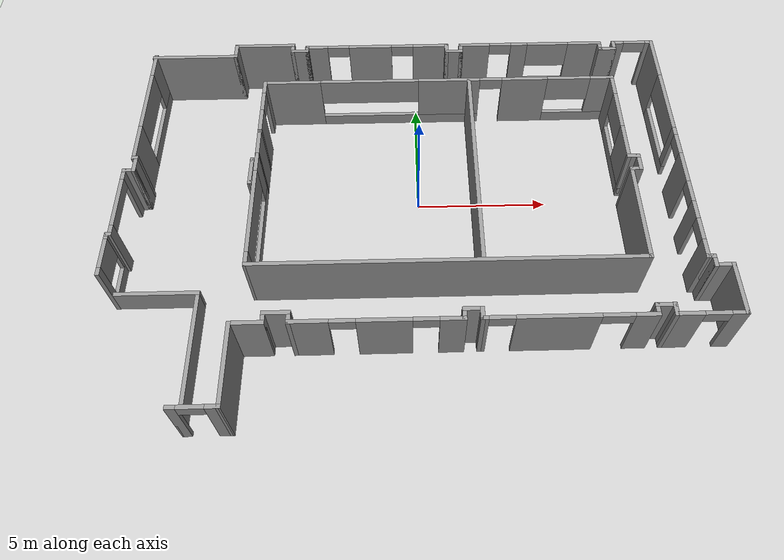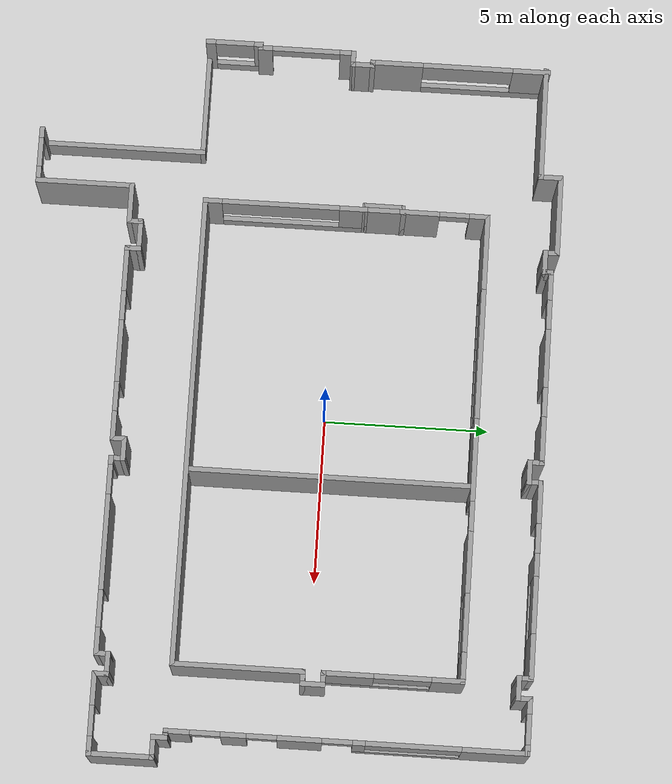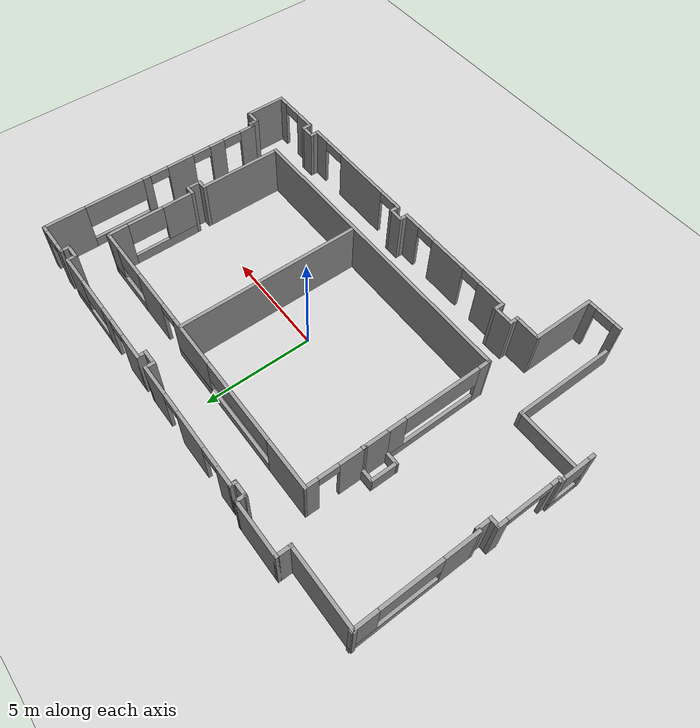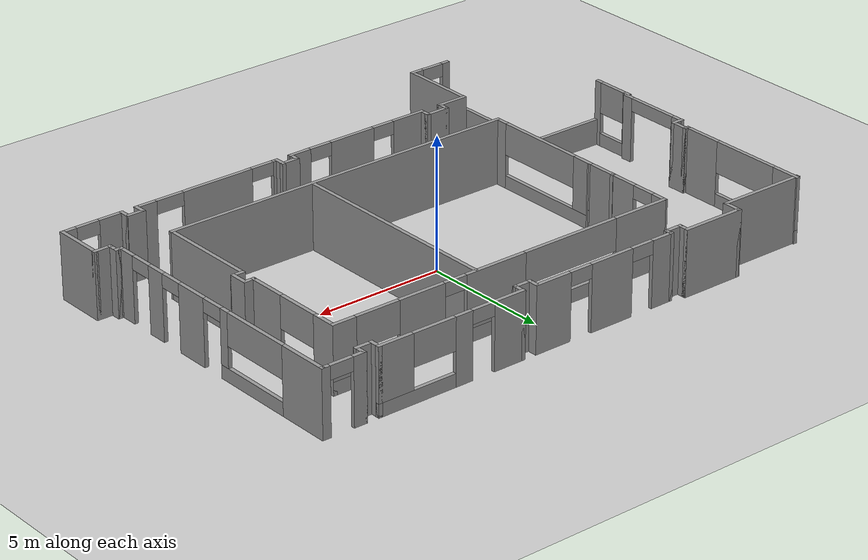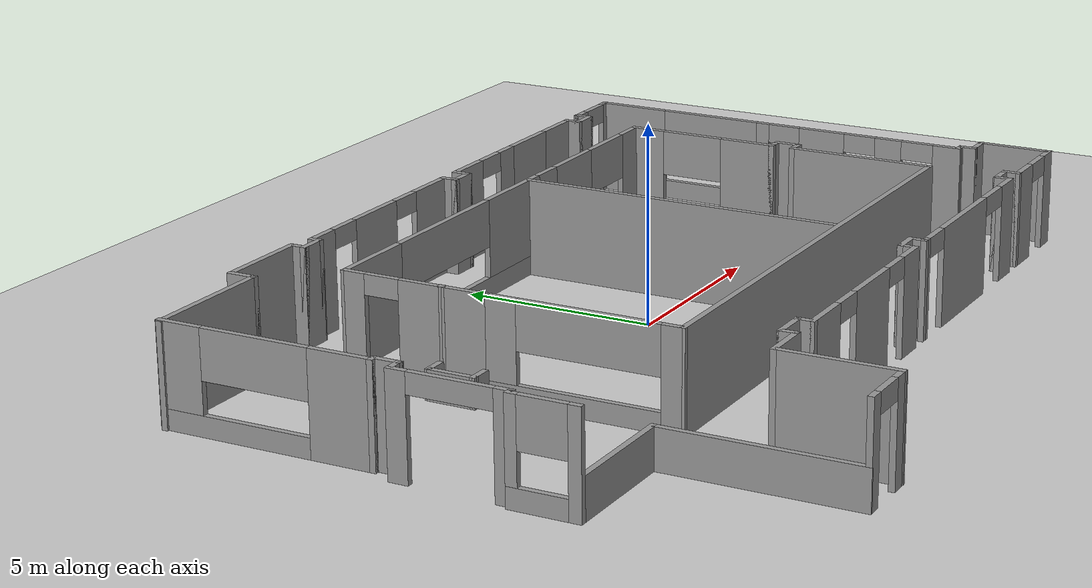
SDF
<sdf version="1.7">
 <world name="default">
  <light name="sun" type="directional">
   <pose>0 0 10 0 -0 0</pose>
   <diffuse>0.8 0.8 0.8 1</diffuse>
   <specular>0.2 0.2 0.2 1</specular>
   <attenuation>
    <range>1000</range>
    <constant>0.9</constant>
    <linear>0.01</linear>
    <quadratic>0.001</quadratic>
   </attenuation>
   <direction>-0.5 0.1 -0.9</direction>
   <spot><inner_angle>0</inner_angle><outer_angle>0</outer_angle><falloff>0</falloff></spot>
  </light>
  <model name="ground_plane">
   <static>1</static>
   <link name="link">
    <collision name="collision">
     <geometry><plane><normal>0 0 1</normal><size>100 100</size></plane></geometry>
     <surface>
      <contact><collide_bitmask>65535</collide_bitmask></contact>
      <friction><ode><mu>100</mu><mu2>50</mu2></ode></friction>
     </surface>
    </collision>
    <visual name="visual">
     <cast_shadows>0</cast_shadows>
     <geometry><plane><normal>0 0 1</normal><size>100 100</size></plane></geometry>
     <material>
      <script><uri>file://media/materials/scripts/gazebo.material</uri><name>Gazebo/Grey</name></script>
     </material>
    </visual>
   </link>
  </model>
  <gravity>0 0 -9.8</gravity>
  <magnetic_field>6e-06 2.3e-05 -4.2e-05</magnetic_field>
  <atmosphere type="adiabatic"/>
  <physics type="ode">
   <max_step_size>0.001</max_step_size>
   <real_time_factor>1</real_time_factor>
   <real_time_update_rate>1000</real_time_update_rate>
  </physics>
  <scene><ambient>0.4 0.4 0.4 1</ambient><background>0.7 0.7 0.7 1</background><shadows>1</shadows></scene>
  <spherical_coordinates>
   <surface_model>EARTH_WGS84</surface_model>
   <latitude_deg>0</latitude_deg>
   <longitude_deg>0</longitude_deg>
   <elevation>0</elevation>
   <heading_deg>0</heading_deg>
  </spherical_coordinates>
  <model name="Meam">
   <pose>-0.181927 -1.20412 0 0 -0 0</pose>
   <link name="Wall_10">
    <collision name="Wall_10_Collision">
     <geometry><box><size>0.75 0.15 2.5</size></box></geometry>
     <pose>0 0 1.25 0 -0 0</pose>
    </collision>
    <visual name="Wall_10_Visual">
     <pose>0 0 1.25 0 -0 0</pose>
     <geometry><box><size>0.75 0.15 2.5</size></box></geometry>
     <material>
      <script><uri>file://media/materials/scripts/gazebo.material</uri><name>Gazebo/Grey</name></script>
      <ambient>1 1 1 1</ambient>
     </material>
     <meta><layer>0</layer></meta>
    </visual>
    <pose>8.51312 1.35218 0 0 -0 -1.5708</pose>
   </link>
   <link name="Wall_101">
    <collision name="Wall_101_Collision">
     <geometry><box><size>0.15 0.15 2.5</size></box></geometry>
     <pose>0 0 1.25 0 -0 0</pose>
    </collision>
    <visual name="Wall_101_Visual">
     <pose>0 0 1.25 0 -0 0</pose>
     <geometry><box><size>0.15 0.15 2.5</size></box></geometry>
     <material>
      <script><uri>file://media/materials/scripts/gazebo.material</uri><name>Gazebo/Grey</name></script>
      <ambient>1 1 1 1</ambient>
     </material>
     <meta><layer>0</layer></meta>
    </visual>
    <pose>-5.93207 3.20912 0 0 -0 0</pose>
   </link>
   <link name="Wall_102">
    <collision name="Wall_102_Collision">
     <geometry><box><size>0.15 0.15 2.5</size></box></geometry>
     <pose>0 0 1.25 0 -0 0</pose>
    </collision>
    <visual name="Wall_102_Visual">
     <pose>0 0 1.25 0 -0 0</pose>
     <geometry><box><size>0.15 0.15 2.5</size></box></geometry>
     <material>
      <script><uri>file://media/materials/scripts/gazebo.material</uri><name>Gazebo/Grey</name></script>
      <ambient>1 1 1 1</ambient>
     </material>
     <meta><layer>0</layer></meta>
    </visual>
    <pose>-5.93207 3.20912 0 0 -0 0</pose>
   </link>
   <link name="Wall_13">
    <collision name="Wall_13_Collision">
     <geometry><box><size>0.5 0.15 2.5</size></box></geometry>
     <pose>0 0 1.25 0 -0 0</pose>
    </collision>
    <visual name="Wall_13_Visual">
     <pose>0 0 1.25 0 -0 0</pose>
     <geometry><box><size>0.5 0.15 2.5</size></box></geometry>
     <material>
      <script><uri>file://media/materials/scripts/gazebo.material</uri><name>Gazebo/Grey</name></script>
      <ambient>1 1 1 1</ambient>
     </material>
     <meta><layer>0</layer></meta>
    </visual>
    <pose>8.33812 1.05218 0 0 -0 3.14159</pose>
   </link>
   <link name="Wall_15">
    <collision name="Wall_15_Collision">
     <geometry><box><size>4 0.15 2.5</size></box></geometry>
     <pose>0 0 1.25 0 -0 0</pose>
    </collision>
    <visual name="Wall_15_Visual">
     <pose>0 0 1.25 0 -0 0</pose>
     <geometry><box><size>4 0.15 2.5</size></box></geometry>
     <material>
      <script><uri>file://media/materials/scripts/gazebo.material</uri><name>Gazebo/Grey</name></script>
      <ambient>1 1 1 1</ambient>
     </material>
     <meta><layer>0</layer></meta>
    </visual>
    <pose>8.16313 -0.872824 0 0 -0 -1.5708</pose>
   </link>
   <link name="Wall_16">
    <collision name="Wall_16_Collision">
     <geometry><box><size>14.25 0.15 2.5</size></box></geometry>
     <pose>0 0 1.25 0 -0 0</pose>
    </collision>
    <visual name="Wall_16_Visual">
     <pose>0 0 1.25 0 -0 0</pose>
     <geometry><box><size>14.25 0.15 2.5</size></box></geometry>
     <material>
      <script><uri>file://media/materials/scripts/gazebo.material</uri><name>Gazebo/Grey</name></script>
      <ambient>1 1 1 1</ambient>
     </material>
     <meta><layer>0</layer></meta>
    </visual>
    <pose>1.11312 -2.79782 0 0 -0 3.14159</pose>
   </link>
   <link name="Wall_17">
    <pose>-5.93987 -0.373959 0 0 -0 1.57203</pose>
    <visual name="Wall_17_Visual_0">
     <pose>-2.20713 0 1.25 0 -0 0</pose>
     <geometry><box><size>0.583489 0.15 2.5</size></box></geometry>
     <material>
      <script><uri>file://media/materials/scripts/gazebo.material</uri><name>Gazebo/Grey</name></script>
      <ambient>1 1 1 1</ambient>
     </material>
     <meta><layer>0</layer></meta>
    </visual>
    <collision name="Wall_17_Collision_0">
     <geometry><box><size>0.583489 0.15 2.5</size></box></geometry>
     <pose>-2.20713 0 1.25 0 -0 0</pose>
    </collision>
    <visual name="Wall_17_Visual_1">
     <pose>0.291745 0 0.25 0 -0 0</pose>
     <geometry><box><size>4.41426 0.15 0.5</size></box></geometry>
     <material>
      <script><uri>file://media/materials/scripts/gazebo.material</uri><name>Gazebo/Grey</name></script>
      <ambient>1 1 1 1</ambient>
     </material>
     <meta><layer>0</layer></meta>
    </visual>
    <collision name="Wall_17_Collision_1">
     <geometry><box><size>4.41426 0.15 0.5</size></box></geometry>
     <pose>0.291745 0 0.25 0 -0 0</pose>
    </collision>
    <visual name="Wall_17_Visual_2">
     <pose>2.07174 0 1.5 0 -0 0</pose>
     <geometry><box><size>0.854258 0.15 2</size></box></geometry>
     <material>
      <script><uri>file://media/materials/scripts/gazebo.material</uri><name>Gazebo/Grey</name></script>
      <ambient>1 1 1 1</ambient>
     </material>
     <meta><layer>0</layer></meta>
    </visual>
    <collision name="Wall_17_Collision_2">
     <geometry><box><size>0.854258 0.15 2</size></box></geometry>
     <pose>2.07174 0 1.5 0 -0 0</pose>
    </collision>
    <visual name="Wall_17_Visual_3">
     <pose>-0.135384 0 1.9 0 -0 0</pose>
     <geometry><box><size>3.56 0.15 1.2</size></box></geometry>
     <material>
      <script><uri>file://media/materials/scripts/gazebo.material</uri><name>Gazebo/Grey</name></script>
      <ambient>1 1 1 1</ambient>
     </material>
     <meta><layer>0</layer></meta>
    </visual>
    <collision name="Wall_17_Collision_3">
     <geometry><box><size>3.56 0.15 1.2</size></box></geometry>
     <pose>-0.135384 0 1.9 0 -0 0</pose>
    </collision>
   </link>
   <link name="Wall_18">
    <collision name="Wall_18_Collision">
     <geometry><box><size>0.75 0.15 0.75</size></box></geometry>
     <pose>0 0 0.375 0 -0 0</pose>
    </collision>
    <visual name="Wall_18_Visual">
     <pose>0 0 0.375 0 -0 0</pose>
     <geometry><box><size>0.75 0.15 0.75</size></box></geometry>
     <material>
      <script><uri>file://media/materials/scripts/gazebo.material</uri><name>Gazebo/Grey</name></script>
      <ambient>1 1 1 1</ambient>
     </material>
     <meta><layer>0</layer></meta>
    </visual>
    <pose>-6.24286 2.05102 0 0 -0 3.13787</pose>
   </link>
   <link name="Wall_22">
    <pose>-5.94096 4.45754 0 0 -0 1.56764</pose>
    <visual name="Wall_22_Visual_0">
     <pose>-0.763537 0 1.25 0 -0 0</pose>
     <geometry><box><size>1.21225 0.15 2.5</size></box></geometry>
     <material>
      <script><uri>file://media/materials/scripts/gazebo.material</uri><name>Gazebo/Grey</name></script>
      <ambient>1 1 1 1</ambient>
     </material>
     <meta><layer>0</layer></meta>
    </visual>
    <collision name="Wall_22_Collision_0">
     <geometry><box><size>1.21225 0.15 2.5</size></box></geometry>
     <pose>-0.763537 0 1.25 0 -0 0</pose>
    </collision>
    <visual name="Wall_22_Visual_1">
     <pose>1.05612 0 1.25 0 -0 0</pose>
     <geometry><box><size>0.627073 0.15 2.5</size></box></geometry>
     <material>
      <script><uri>file://media/materials/scripts/gazebo.material</uri><name>Gazebo/Grey</name></script>
      <ambient>1 1 1 1</ambient>
     </material>
     <meta><layer>0</layer></meta>
    </visual>
    <collision name="Wall_22_Collision_1">
     <geometry><box><size>0.627073 0.15 2.5</size></box></geometry>
     <pose>1.05612 0 1.25 0 -0 0</pose>
    </collision>
    <visual name="Wall_22_Visual_2">
     <pose>0.292587 0 2.25 0 -0 0</pose>
     <geometry><box><size>0.9 0.15 0.5</size></box></geometry>
     <material>
      <script><uri>file://media/materials/scripts/gazebo.material</uri><name>Gazebo/Grey</name></script>
      <ambient>1 1 1 1</ambient>
     </material>
     <meta><layer>0</layer></meta>
    </visual>
    <collision name="Wall_22_Collision_2">
     <geometry><box><size>0.9 0.15 0.5</size></box></geometry>
     <pose>0.292587 0 2.25 0 -0 0</pose>
    </collision>
   </link>
   <link name="Wall_24">
    <collision name="Wall_24_Collision">
     <geometry><box><size>3.5 0.15 2.5</size></box></geometry>
     <pose>0 0 1.25 0 -0 0</pose>
    </collision>
    <visual name="Wall_24_Visual">
     <pose>0 0 1.25 0 -0 0</pose>
     <geometry><box><size>3.5 0.15 2.5</size></box></geometry>
     <material>
      <script><uri>file://media/materials/scripts/gazebo.material</uri><name>Gazebo/Grey</name></script>
      <ambient>1 1 1 1</ambient>
     </material>
     <meta><layer>0</layer></meta>
    </visual>
    <pose>-8.97492 7.3 0 0 -0 0</pose>
   </link>
   <link name="Wall_25">
    <collision name="Wall_25_Collision">
     <geometry><box><size>0.75 0.15 2.5</size></box></geometry>
     <pose>0 0 1.25 0 -0 0</pose>
    </collision>
    <visual name="Wall_25_Visual">
     <pose>0 0 1.25 0 -0 0</pose>
     <geometry><box><size>0.75 0.15 2.5</size></box></geometry>
     <material>
      <script><uri>file://media/materials/scripts/gazebo.material</uri><name>Gazebo/Grey</name></script>
      <ambient>1 1 1 1</ambient>
     </material>
     <meta><layer>0</layer></meta>
    </visual>
    <pose>-7.29992 7.6 0 0 -0 1.5708</pose>
   </link>
   <link name="Wall_26">
    <collision name="Wall_26_Collision">
     <geometry><box><size>2.5 0.15 2.5</size></box></geometry>
     <pose>0 0 1.25 0 -0 0</pose>
    </collision>
    <visual name="Wall_26_Visual">
     <pose>0 0 1.25 0 -0 0</pose>
     <geometry><box><size>2.5 0.15 2.5</size></box></geometry>
     <material>
      <script><uri>file://media/materials/scripts/gazebo.material</uri><name>Gazebo/Grey</name></script>
      <ambient>1 1 1 1</ambient>
     </material>
     <meta><layer>0</layer></meta>
    </visual>
    <pose>-6.12492 7.9 0 0 -0 0</pose>
   </link>
   <link name="Wall_27">
    <collision name="Wall_27_Collision">
     <geometry><box><size>0.5 0.15 2.5</size></box></geometry>
     <pose>0 0 1.25 0 -0 0</pose>
    </collision>
    <visual name="Wall_27_Visual">
     <pose>0 0 1.25 0 -0 0</pose>
     <geometry><box><size>0.5 0.15 2.5</size></box></geometry>
     <material>
      <script><uri>file://media/materials/scripts/gazebo.material</uri><name>Gazebo/Grey</name></script>
      <ambient>1 1 1 1</ambient>
     </material>
     <meta><layer>0</layer></meta>
    </visual>
    <pose>-4.94992 7.725 0 0 -0 -1.5708</pose>
   </link>
   <link name="Wall_28">
    <collision name="Wall_28_Collision">
     <geometry><box><size>0.75 0.15 2.5</size></box></geometry>
     <pose>0 0 1.25 0 -0 0</pose>
    </collision>
    <visual name="Wall_28_Visual">
     <pose>0 0 1.25 0 -0 0</pose>
     <geometry><box><size>0.75 0.15 2.5</size></box></geometry>
     <material>
      <script><uri>file://media/materials/scripts/gazebo.material</uri><name>Gazebo/Grey</name></script>
      <ambient>1 1 1 1</ambient>
     </material>
     <meta><layer>0</layer></meta>
    </visual>
    <pose>-4.64992 7.55 0 0 -0 0</pose>
   </link>
   <link name="Wall_29">
    <collision name="Wall_29_Collision">
     <geometry><box><size>0.25 0.15 2.5</size></box></geometry>
     <pose>0 0 1.25 0 -0 0</pose>
    </collision>
    <visual name="Wall_29_Visual">
     <pose>0 0 1.25 0 -0 0</pose>
     <geometry><box><size>0.25 0.15 2.5</size></box></geometry>
     <material>
      <script><uri>file://media/materials/scripts/gazebo.material</uri><name>Gazebo/Grey</name></script>
      <ambient>1 1 1 1</ambient>
     </material>
     <meta><layer>0</layer></meta>
    </visual>
    <pose>-4.34992 7.6 0 0 -0 1.5708</pose>
   </link>
   <link name="Wall_30">
    <collision name="Wall_30_Collision">
     <geometry><box><size>0.25 0.15 2.5</size></box></geometry>
     <pose>0 0 1.25 0 -0 0</pose>
    </collision>
    <visual name="Wall_30_Visual">
     <pose>0 0 1.25 0 -0 0</pose>
     <geometry><box><size>0.25 0.15 2.5</size></box></geometry>
     <material>
      <script><uri>file://media/materials/scripts/gazebo.material</uri><name>Gazebo/Grey</name></script>
      <ambient>1 1 1 1</ambient>
     </material>
     <meta><layer>0</layer></meta>
    </visual>
    <pose>-4.34992 7.7 0 0 -0 1.5708</pose>
   </link>
   <link name="Wall_31">
    <pose>-1.42492 7.75 0 0 -0 0</pose>
    <visual name="Wall_31_Visual_0">
     <pose>-2.53292 0 1.25 0 -0 0</pose>
     <geometry><box><size>0.934165 0.15 2.5</size></box></geometry>
     <material>
      <script><uri>file://media/materials/scripts/gazebo.material</uri><name>Gazebo/Grey</name></script>
      <ambient>1 1 1 1</ambient>
     </material>
     <meta><layer>0</layer></meta>
    </visual>
    <collision name="Wall_31_Collision_0">
     <geometry><box><size>0.934165 0.15 2.5</size></box></geometry>
     <pose>-2.53292 0 1.25 0 -0 0</pose>
    </collision>
    <visual name="Wall_31_Visual_1">
     <pose>-0.274502 0 1.25 0 -0 0</pose>
     <geometry><box><size>1.78267 0.15 2.5</size></box></geometry>
     <material>
      <script><uri>file://media/materials/scripts/gazebo.material</uri><name>Gazebo/Grey</name></script>
      <ambient>1 1 1 1</ambient>
     </material>
     <meta><layer>0</layer></meta>
    </visual>
    <collision name="Wall_31_Collision_1">
     <geometry><box><size>1.78267 0.15 2.5</size></box></geometry>
     <pose>-0.274502 0 1.25 0 -0 0</pose>
    </collision>
    <visual name="Wall_31_Visual_2">
     <pose>2.25841 0 1.25 0 -0 0</pose>
     <geometry><box><size>1.48317 0.15 2.5</size></box></geometry>
     <material>
      <script><uri>file://media/materials/scripts/gazebo.material</uri><name>Gazebo/Grey</name></script>
      <ambient>1 1 1 1</ambient>
     </material>
     <meta><layer>0</layer></meta>
    </visual>
    <collision name="Wall_31_Collision_2">
     <geometry><box><size>1.48317 0.15 2.5</size></box></geometry>
     <pose>2.25841 0 1.25 0 -0 0</pose>
    </collision>
    <visual name="Wall_31_Visual_3">
     <pose>-1.61583 0 2.25 0 -0 0</pose>
     <geometry><box><size>0.9 0.15 0.5</size></box></geometry>
     <material>
      <script><uri>file://media/materials/scripts/gazebo.material</uri><name>Gazebo/Grey</name></script>
      <ambient>1 1 1 1</ambient>
     </material>
     <meta><layer>0</layer></meta>
    </visual>
    <collision name="Wall_31_Collision_3">
     <geometry><box><size>0.9 0.15 0.5</size></box></geometry>
     <pose>-1.61583 0 2.25 0 -0 0</pose>
    </collision>
    <visual name="Wall_31_Visual_4">
     <pose>1.06683 0 2.25 0 -0 0</pose>
     <geometry><box><size>0.9 0.15 0.5</size></box></geometry>
     <material>
      <script><uri>file://media/materials/scripts/gazebo.material</uri><name>Gazebo/Grey</name></script>
      <ambient>1 1 1 1</ambient>
     </material>
     <meta><layer>0</layer></meta>
    </visual>
    <collision name="Wall_31_Collision_4">
     <geometry><box><size>0.9 0.15 0.5</size></box></geometry>
     <pose>1.06683 0 2.25 0 -0 0</pose>
    </collision>
   </link>
   <link name="Wall_32">
    <collision name="Wall_32_Collision">
     <geometry><box><size>0.5 0.15 2.5</size></box></geometry>
     <pose>0 0 1.25 0 -0 0</pose>
    </collision>
    <visual name="Wall_32_Visual">
     <pose>0 0 1.25 0 -0 0</pose>
     <geometry><box><size>0.5 0.15 2.5</size></box></geometry>
     <material>
      <script><uri>file://media/materials/scripts/gazebo.material</uri><name>Gazebo/Grey</name></script>
      <ambient>1 1 1 1</ambient>
     </material>
     <meta><layer>0</layer></meta>
    </visual>
    <pose>1.50008 7.575 0 0 -0 -1.5708</pose>
   </link>
   <link name="Wall_33">
    <collision name="Wall_33_Collision">
     <geometry><box><size>0.75 0.15 2.5</size></box></geometry>
     <pose>0 0 1.25 0 -0 0</pose>
    </collision>
    <visual name="Wall_33_Visual">
     <pose>0 0 1.25 0 -0 0</pose>
     <geometry><box><size>0.75 0.15 2.5</size></box></geometry>
     <material>
      <script><uri>file://media/materials/scripts/gazebo.material</uri><name>Gazebo/Grey</name></script>
      <ambient>1 1 1 1</ambient>
     </material>
     <meta><layer>0</layer></meta>
    </visual>
    <pose>1.80008 7.4 0 0 -0 0</pose>
   </link>
   <link name="Wall_34">
    <collision name="Wall_34_Collision">
     <geometry><box><size>0.5 0.15 2.5</size></box></geometry>
     <pose>0 0 1.25 0 -0 0</pose>
    </collision>
    <visual name="Wall_34_Visual">
     <pose>0 0 1.25 0 -0 0</pose>
     <geometry><box><size>0.5 0.15 2.5</size></box></geometry>
     <material>
      <script><uri>file://media/materials/scripts/gazebo.material</uri><name>Gazebo/Grey</name></script>
      <ambient>1 1 1 1</ambient>
     </material>
     <meta><layer>0</layer></meta>
    </visual>
    <pose>2.10008 7.575 0 0 -0 1.5708</pose>
   </link>
   <link name="Wall_35">
    <pose>5.02508 7.75 0 0 -0 0</pose>
    <visual name="Wall_35_Visual_0">
     <pose>-2.35198 0 1.25 0 -0 0</pose>
     <geometry><box><size>1.29603 0.15 2.5</size></box></geometry>
     <material>
      <script><uri>file://media/materials/scripts/gazebo.material</uri><name>Gazebo/Grey</name></script>
      <ambient>1 1 1 1</ambient>
     </material>
     <meta><layer>0</layer></meta>
    </visual>
    <collision name="Wall_35_Collision_0">
     <geometry><box><size>1.29603 0.15 2.5</size></box></geometry>
     <pose>-2.35198 0 1.25 0 -0 0</pose>
    </collision>
    <visual name="Wall_35_Visual_1">
     <pose>-0.459673 0 1.25 0 -0 0</pose>
     <geometry><box><size>0.688588 0.15 2.5</size></box></geometry>
     <material>
      <script><uri>file://media/materials/scripts/gazebo.material</uri><name>Gazebo/Grey</name></script>
      <ambient>1 1 1 1</ambient>
     </material>
     <meta><layer>0</layer></meta>
    </visual>
    <collision name="Wall_35_Collision_1">
     <geometry><box><size>0.688588 0.15 2.5</size></box></geometry>
     <pose>-0.459673 0 1.25 0 -0 0</pose>
    </collision>
    <visual name="Wall_35_Visual_2">
     <pose>1.44231 0 0.25 0 -0 0</pose>
     <geometry><box><size>3.11538 0.15 0.5</size></box></geometry>
     <material>
      <script><uri>file://media/materials/scripts/gazebo.material</uri><name>Gazebo/Grey</name></script>
      <ambient>1 1 1 1</ambient>
     </material>
     <meta><layer>0</layer></meta>
    </visual>
    <collision name="Wall_35_Collision_2">
     <geometry><box><size>3.11538 0.15 0.5</size></box></geometry>
     <pose>1.44231 0 0.25 0 -0 0</pose>
    </collision>
    <visual name="Wall_35_Visual_3">
     <pose>2.296 0 1.5 0 -0 0</pose>
     <geometry><box><size>1.40801 0.15 2</size></box></geometry>
     <material>
      <script><uri>file://media/materials/scripts/gazebo.material</uri><name>Gazebo/Grey</name></script>
      <ambient>1 1 1 1</ambient>
     </material>
     <meta><layer>0</layer></meta>
    </visual>
    <collision name="Wall_35_Collision_3">
     <geometry><box><size>1.40801 0.15 2</size></box></geometry>
     <pose>2.296 0 1.5 0 -0 0</pose>
    </collision>
    <visual name="Wall_35_Visual_4">
     <pose>0.738307 0 1.9 0 -0 0</pose>
     <geometry><box><size>1.70737 0.15 1.2</size></box></geometry>
     <material>
      <script><uri>file://media/materials/scripts/gazebo.material</uri><name>Gazebo/Grey</name></script>
      <ambient>1 1 1 1</ambient>
     </material>
     <meta><layer>0</layer></meta>
    </visual>
    <collision name="Wall_35_Collision_4">
     <geometry><box><size>1.70737 0.15 1.2</size></box></geometry>
     <pose>0.738307 0 1.9 0 -0 0</pose>
    </collision>
    <visual name="Wall_35_Visual_5">
     <pose>-1.25397 0 2.25 0 -0 0</pose>
     <geometry><box><size>0.9 0.15 0.5</size></box></geometry>
     <material>
      <script><uri>file://media/materials/scripts/gazebo.material</uri><name>Gazebo/Grey</name></script>
      <ambient>1 1 1 1</ambient>
     </material>
     <meta><layer>0</layer></meta>
    </visual>
    <collision name="Wall_35_Collision_5">
     <geometry><box><size>0.9 0.15 0.5</size></box></geometry>
     <pose>-1.25397 0 2.25 0 -0 0</pose>
    </collision>
   </link>
   <link name="Wall_36">
    <collision name="Wall_36_Collision">
     <geometry><box><size>0.5 0.15 2.5</size></box></geometry>
     <pose>0 0 1.25 0 -0 0</pose>
    </collision>
    <visual name="Wall_36_Visual">
     <pose>0 0 1.25 0 -0 0</pose>
     <geometry><box><size>0.5 0.15 2.5</size></box></geometry>
     <material>
      <script><uri>file://media/materials/scripts/gazebo.material</uri><name>Gazebo/Grey</name></script>
      <ambient>1 1 1 1</ambient>
     </material>
     <meta><layer>0</layer></meta>
    </visual>
    <pose>7.95008 7.575 0 0 -0 -1.5708</pose>
   </link>
   <link name="Wall_37">
    <collision name="Wall_37_Collision">
     <geometry><box><size>0.75 0.15 2.5</size></box></geometry>
     <pose>0 0 1.25 0 -0 0</pose>
    </collision>
    <visual name="Wall_37_Visual">
     <pose>0 0 1.25 0 -0 0</pose>
     <geometry><box><size>0.75 0.15 2.5</size></box></geometry>
     <material>
      <script><uri>file://media/materials/scripts/gazebo.material</uri><name>Gazebo/Grey</name></script>
      <ambient>1 1 1 1</ambient>
     </material>
     <meta><layer>0</layer></meta>
    </visual>
    <pose>8.25008 7.4 0 0 -0 0</pose>
   </link>
   <link name="Wall_38">
    <collision name="Wall_38_Collision">
     <geometry><box><size>0.5 0.15 2.5</size></box></geometry>
     <pose>0 0 1.25 0 -0 0</pose>
    </collision>
    <visual name="Wall_38_Visual">
     <pose>0 0 1.25 0 -0 0</pose>
     <geometry><box><size>0.5 0.15 2.5</size></box></geometry>
     <material>
      <script><uri>file://media/materials/scripts/gazebo.material</uri><name>Gazebo/Grey</name></script>
      <ambient>1 1 1 1</ambient>
     </material>
     <meta><layer>0</layer></meta>
    </visual>
    <pose>8.55008 7.575 0 0 -0 1.5708</pose>
   </link>
   <link name="Wall_39">
    <pose>9.35008 7.75 0 0 -0 0</pose>
    <visual name="Wall_39_Visual_0">
     <pose>-0.618089 0 1.25 0 -0 0</pose>
     <geometry><box><size>0.513822 0.15 2.5</size></box></geometry>
     <material>
      <script><uri>file://media/materials/scripts/gazebo.material</uri><name>Gazebo/Grey</name></script>
      <ambient>1 1 1 1</ambient>
     </material>
     <meta><layer>0</layer></meta>
    </visual>
    <collision name="Wall_39_Collision_0">
     <geometry><box><size>0.513822 0.15 2.5</size></box></geometry>
     <pose>-0.618089 0 1.25 0 -0 0</pose>
    </collision>
    <visual name="Wall_39_Visual_1">
     <pose>0.706911 0 1.25 0 -0 0</pose>
     <geometry><box><size>0.336178 0.15 2.5</size></box></geometry>
     <material>
      <script><uri>file://media/materials/scripts/gazebo.material</uri><name>Gazebo/Grey</name></script>
      <ambient>1 1 1 1</ambient>
     </material>
     <meta><layer>0</layer></meta>
    </visual>
    <collision name="Wall_39_Collision_1">
     <geometry><box><size>0.336178 0.15 2.5</size></box></geometry>
     <pose>0.706911 0 1.25 0 -0 0</pose>
    </collision>
    <visual name="Wall_39_Visual_2">
     <pose>0.088822 0 2.25 0 -0 0</pose>
     <geometry><box><size>0.9 0.15 0.5</size></box></geometry>
     <material>
      <script><uri>file://media/materials/scripts/gazebo.material</uri><name>Gazebo/Grey</name></script>
      <ambient>1 1 1 1</ambient>
     </material>
     <meta><layer>0</layer></meta>
    </visual>
    <collision name="Wall_39_Collision_2">
     <geometry><box><size>0.9 0.15 0.5</size></box></geometry>
     <pose>0.088822 0 2.25 0 -0 0</pose>
    </collision>
   </link>
   <link name="Wall_41">
    <pose>10.1501 2.45 0 0 -0 -1.5708</pose>
    <visual name="Wall_41_Visual_0">
     <pose>-4.37739 0 1.25 0 -0 0</pose>
     <geometry><box><size>1.99521 0.15 2.5</size></box></geometry>
     <material>
      <script><uri>file://media/materials/scripts/gazebo.material</uri><name>Gazebo/Grey</name></script>
      <ambient>1 1 1 1</ambient>
     </material>
     <meta><layer>0</layer></meta>
    </visual>
    <collision name="Wall_41_Collision_0">
     <geometry><box><size>1.99521 0.15 2.5</size></box></geometry>
     <pose>-4.37739 0 1.25 0 -0 0</pose>
    </collision>
    <visual name="Wall_41_Visual_1">
     <pose>1.37954 0 1.25 0 -0 0</pose>
     <geometry><box><size>1.32241 0.15 2.5</size></box></geometry>
     <material>
      <script><uri>file://media/materials/scripts/gazebo.material</uri><name>Gazebo/Grey</name></script>
      <ambient>1 1 1 1</ambient>
     </material>
     <meta><layer>0</layer></meta>
    </visual>
    <collision name="Wall_41_Collision_1">
     <geometry><box><size>1.32241 0.15 2.5</size></box></geometry>
     <pose>1.37954 0 1.25 0 -0 0</pose>
    </collision>
    <visual name="Wall_41_Visual_2">
     <pose>3.31922 0 1.25 0 -0 0</pose>
     <geometry><box><size>0.756941 0.15 2.5</size></box></geometry>
     <material>
      <script><uri>file://media/materials/scripts/gazebo.material</uri><name>Gazebo/Grey</name></script>
      <ambient>1 1 1 1</ambient>
     </material>
     <meta><layer>0</layer></meta>
    </visual>
    <collision name="Wall_41_Collision_2">
     <geometry><box><size>0.756941 0.15 2.5</size></box></geometry>
     <pose>3.31922 0 1.25 0 -0 0</pose>
    </collision>
    <visual name="Wall_41_Visual_3">
     <pose>4.98634 0 1.25 0 -0 0</pose>
     <geometry><box><size>0.777313 0.15 2.5</size></box></geometry>
     <material>
      <script><uri>file://media/materials/scripts/gazebo.material</uri><name>Gazebo/Grey</name></script>
      <ambient>1 1 1 1</ambient>
     </material>
     <meta><layer>0</layer></meta>
    </visual>
    <collision name="Wall_41_Collision_3">
     <geometry><box><size>0.777313 0.15 2.5</size></box></geometry>
     <pose>4.98634 0 1.25 0 -0 0</pose>
    </collision>
    <visual name="Wall_41_Visual_4">
     <pose>-1.78072 0 0.25 0 -0 0</pose>
     <geometry><box><size>3.19813 0.15 0.5</size></box></geometry>
     <material>
      <script><uri>file://media/materials/scripts/gazebo.material</uri><name>Gazebo/Grey</name></script>
      <ambient>1 1 1 1</ambient>
     </material>
     <meta><layer>0</layer></meta>
    </visual>
    <collision name="Wall_41_Collision_4">
     <geometry><box><size>3.19813 0.15 0.5</size></box></geometry>
     <pose>-1.78072 0 0.25 0 -0 0</pose>
    </collision>
    <visual name="Wall_41_Visual_5">
     <pose>-0.368148 0 1.5 0 -0 0</pose>
     <geometry><box><size>0.37298 0.15 2</size></box></geometry>
     <material>
      <script><uri>file://media/materials/scripts/gazebo.material</uri><name>Gazebo/Grey</name></script>
      <ambient>1 1 1 1</ambient>
     </material>
     <meta><layer>0</layer></meta>
    </visual>
    <collision name="Wall_41_Collision_5">
     <geometry><box><size>0.37298 0.15 2</size></box></geometry>
     <pose>-0.368148 0 1.5 0 -0 0</pose>
    </collision>
    <visual name="Wall_41_Visual_6">
     <pose>-1.96721 0 1.9 0 -0 0</pose>
     <geometry><box><size>2.82515 0.15 1.2</size></box></geometry>
     <material>
      <script><uri>file://media/materials/scripts/gazebo.material</uri><name>Gazebo/Grey</name></script>
      <ambient>1 1 1 1</ambient>
     </material>
     <meta><layer>0</layer></meta>
    </visual>
    <collision name="Wall_41_Collision_6">
     <geometry><box><size>2.82515 0.15 1.2</size></box></geometry>
     <pose>-1.96721 0 1.9 0 -0 0</pose>
    </collision>
    <visual name="Wall_41_Visual_7">
     <pose>2.49075 0 2.25 0 -0 0</pose>
     <geometry><box><size>0.9 0.15 0.5</size></box></geometry>
     <material>
      <script><uri>file://media/materials/scripts/gazebo.material</uri><name>Gazebo/Grey</name></script>
      <ambient>1 1 1 1</ambient>
     </material>
     <meta><layer>0</layer></meta>
    </visual>
    <collision name="Wall_41_Collision_7">
     <geometry><box><size>0.9 0.15 0.5</size></box></geometry>
     <pose>2.49075 0 2.25 0 -0 0</pose>
    </collision>
    <visual name="Wall_41_Visual_8">
     <pose>4.14769 0 2.25 0 -0 0</pose>
     <geometry><box><size>0.9 0.15 0.5</size></box></geometry>
     <material>
      <script><uri>file://media/materials/scripts/gazebo.material</uri><name>Gazebo/Grey</name></script>
      <ambient>1 1 1 1</ambient>
     </material>
     <meta><layer>0</layer></meta>
    </visual>
    <collision name="Wall_41_Collision_8">
     <geometry><box><size>0.9 0.15 0.5</size></box></geometry>
     <pose>4.14769 0 2.25 0 -0 0</pose>
    </collision>
    <visual name="Wall_41_Visual_9">
     <pose>0.268342 0 2.25 0 -0 0</pose>
     <geometry><box><size>0.9 0.15 0.5</size></box></geometry>
     <material>
      <script><uri>file://media/materials/scripts/gazebo.material</uri><name>Gazebo/Grey</name></script>
      <ambient>1 1 1 1</ambient>
     </material>
     <meta><layer>0</layer></meta>
    </visual>
    <collision name="Wall_41_Collision_9">
     <geometry><box><size>0.9 0.15 0.5</size></box></geometry>
     <pose>0.268342 0 2.25 0 -0 0</pose>
    </collision>
   </link>
   <link name="Wall_44">
    <collision name="Wall_44_Collision">
     <geometry><box><size>0.25 0.15 2.5</size></box></geometry>
     <pose>0 0 1.25 0 -0 0</pose>
    </collision>
    <visual name="Wall_44_Visual">
     <pose>0 0 1.25 0 -0 0</pose>
     <geometry><box><size>0.25 0.15 2.5</size></box></geometry>
     <material>
      <script><uri>file://media/materials/scripts/gazebo.material</uri><name>Gazebo/Grey</name></script>
      <ambient>1 1 1 1</ambient>
     </material>
     <meta><layer>0</layer></meta>
    </visual>
    <pose>10.2001 -2.85 0 0 -0 0</pose>
   </link>
   <link name="Wall_45">
    <collision name="Wall_45_Collision">
     <geometry><box><size>0.25 0.15 2.5</size></box></geometry>
     <pose>0 0 1.25 0 -0 0</pose>
    </collision>
    <visual name="Wall_45_Visual">
     <pose>0 0 1.25 0 -0 0</pose>
     <geometry><box><size>0.25 0.15 2.5</size></box></geometry>
     <material>
      <script><uri>file://media/materials/scripts/gazebo.material</uri><name>Gazebo/Grey</name></script>
      <ambient>1 1 1 1</ambient>
     </material>
     <meta><layer>0</layer></meta>
    </visual>
    <pose>10.3001 -2.85 0 0 -0 0</pose>
   </link>
   <link name="Wall_46">
    <collision name="Wall_46_Collision">
     <geometry><box><size>0.5 0.15 2.5</size></box></geometry>
     <pose>0 0 1.25 0 -0 0</pose>
    </collision>
    <visual name="Wall_46_Visual">
     <pose>0 0 1.25 0 -0 0</pose>
     <geometry><box><size>0.5 0.15 2.5</size></box></geometry>
     <material>
      <script><uri>file://media/materials/scripts/gazebo.material</uri><name>Gazebo/Grey</name></script>
      <ambient>1 1 1 1</ambient>
     </material>
     <meta><layer>0</layer></meta>
    </visual>
    <pose>10.3501 -3.025 0 0 -0 -1.5708</pose>
   </link>
   <link name="Wall_47">
    <collision name="Wall_47_Collision">
     <geometry><box><size>0.75 0.15 2.5</size></box></geometry>
     <pose>0 0 1.25 0 -0 0</pose>
    </collision>
    <visual name="Wall_47_Visual">
     <pose>0 0 1.25 0 -0 0</pose>
     <geometry><box><size>0.75 0.15 2.5</size></box></geometry>
     <material>
      <script><uri>file://media/materials/scripts/gazebo.material</uri><name>Gazebo/Grey</name></script>
      <ambient>1 1 1 1</ambient>
     </material>
     <meta><layer>0</layer></meta>
    </visual>
    <pose>10.6501 -3.2 0 0 -0 0</pose>
   </link>
   <link name="Wall_49">
    <collision name="Wall_49_Collision">
     <geometry><box><size>2 0.15 2.5</size></box></geometry>
     <pose>0 0 1.25 0 -0 0</pose>
    </collision>
    <visual name="Wall_49_Visual">
     <pose>0 0 1.25 0 -0 0</pose>
     <geometry><box><size>2 0.15 2.5</size></box></geometry>
     <material>
      <script><uri>file://media/materials/scripts/gazebo.material</uri><name>Gazebo/Grey</name></script>
      <ambient>1 1 1 1</ambient>
     </material>
     <meta><layer>0</layer></meta>
    </visual>
    <pose>10.9501 -4.125 0 0 -0 -1.5708</pose>
   </link>
   <link name="Wall_5">
    <pose>1.11312 5.75218 0 0 -0 0</pose>
    <visual name="Wall_5_Visual_0">
     <pose>-5.96899 0 1.25 0 -0 0</pose>
     <geometry><box><size>2.31203 0.15 2.5</size></box></geometry>
     <material>
      <script><uri>file://media/materials/scripts/gazebo.material</uri><name>Gazebo/Grey</name></script>
      <ambient>1 1 1 1</ambient>
     </material>
     <meta><layer>0</layer></meta>
    </visual>
    <collision name="Wall_5_Collision_0">
     <geometry><box><size>2.31203 0.15 2.5</size></box></geometry>
     <pose>-5.96899 0 1.25 0 -0 0</pose>
    </collision>
    <visual name="Wall_5_Visual_1">
     <pose>3.49831 0 1.25 0 -0 0</pose>
     <geometry><box><size>1.85897 0.15 2.5</size></box></geometry>
     <material>
      <script><uri>file://media/materials/scripts/gazebo.material</uri><name>Gazebo/Grey</name></script>
      <ambient>1 1 1 1</ambient>
     </material>
     <meta><layer>0</layer></meta>
    </visual>
    <collision name="Wall_5_Collision_1">
     <geometry><box><size>1.85897 0.15 2.5</size></box></geometry>
     <pose>3.49831 0 1.25 0 -0 0</pose>
    </collision>
    <visual name="Wall_5_Visual_2">
     <pose>-1.57207 0 0.25 0 -0 0</pose>
     <geometry><box><size>6.4818 0.15 0.5</size></box></geometry>
     <material>
      <script><uri>file://media/materials/scripts/gazebo.material</uri><name>Gazebo/Grey</name></script>
      <ambient>1 1 1 1</ambient>
     </material>
     <meta><layer>0</layer></meta>
    </visual>
    <collision name="Wall_5_Collision_2">
     <geometry><box><size>6.4818 0.15 0.5</size></box></geometry>
     <pose>-1.57207 0 0.25 0 -0 0</pose>
    </collision>
    <visual name="Wall_5_Visual_3">
     <pose>5.7764 0 0.25 0 -0 0</pose>
     <geometry><box><size>2.69721 0.15 0.5</size></box></geometry>
     <material>
      <script><uri>file://media/materials/scripts/gazebo.material</uri><name>Gazebo/Grey</name></script>
      <ambient>1 1 1 1</ambient>
     </material>
     <meta><layer>0</layer></meta>
    </visual>
    <collision name="Wall_5_Collision_3">
     <geometry><box><size>2.69721 0.15 0.5</size></box></geometry>
     <pose>5.7764 0 0.25 0 -0 0</pose>
    </collision>
    <visual name="Wall_5_Visual_4">
     <pose>0.414926 0 1.5 0 -0 0</pose>
     <geometry><box><size>2.5078 0.15 2</size></box></geometry>
     <material>
      <script><uri>file://media/materials/scripts/gazebo.material</uri><name>Gazebo/Grey</name></script>
      <ambient>1 1 1 1</ambient>
     </material>
     <meta><layer>0</layer></meta>
    </visual>
    <collision name="Wall_5_Collision_4">
     <geometry><box><size>2.5078 0.15 2</size></box></geometry>
     <pose>0.414926 0 1.5 0 -0 0</pose>
    </collision>
    <visual name="Wall_5_Visual_5">
     <pose>0.414926 0 1.5 0 -0 0</pose>
     <geometry><box><size>2.5078 0.15 2</size></box></geometry>
     <material>
      <script><uri>file://media/materials/scripts/gazebo.material</uri><name>Gazebo/Grey</name></script>
      <ambient>1 1 1 1</ambient>
     </material>
     <meta><layer>0</layer></meta>
    </visual>
    <collision name="Wall_5_Collision_5">
     <geometry><box><size>2.5078 0.15 2</size></box></geometry>
     <pose>0.414926 0 1.5 0 -0 0</pose>
    </collision>
    <visual name="Wall_5_Visual_6">
     <pose>6.64981 0 1.5 0 -0 0</pose>
     <geometry><box><size>0.950384 0.15 2</size></box></geometry>
     <material>
      <script><uri>file://media/materials/scripts/gazebo.material</uri><name>Gazebo/Grey</name></script>
      <ambient>1 1 1 1</ambient>
     </material>
     <meta><layer>0</layer></meta>
    </visual>
    <collision name="Wall_5_Collision_6">
     <geometry><box><size>0.950384 0.15 2</size></box></geometry>
     <pose>6.64981 0 1.5 0 -0 0</pose>
    </collision>
    <visual name="Wall_5_Visual_7">
     <pose>-2.82597 0 1.9 0 -0 0</pose>
     <geometry><box><size>3.974 0.15 1.2</size></box></geometry>
     <material>
      <script><uri>file://media/materials/scripts/gazebo.material</uri><name>Gazebo/Grey</name></script>
      <ambient>1 1 1 1</ambient>
     </material>
     <meta><layer>0</layer></meta>
    </visual>
    <collision name="Wall_5_Collision_7">
     <geometry><box><size>3.974 0.15 1.2</size></box></geometry>
     <pose>-2.82597 0 1.9 0 -0 0</pose>
    </collision>
    <visual name="Wall_5_Visual_8">
     <pose>5.3012 0 1.9 0 -0 0</pose>
     <geometry><box><size>1.74682 0.15 1.2</size></box></geometry>
     <material>
      <script><uri>file://media/materials/scripts/gazebo.material</uri><name>Gazebo/Grey</name></script>
      <ambient>1 1 1 1</ambient>
     </material>
     <meta><layer>0</layer></meta>
    </visual>
    <collision name="Wall_5_Collision_8">
     <geometry><box><size>1.74682 0.15 1.2</size></box></geometry>
     <pose>5.3012 0 1.9 0 -0 0</pose>
    </collision>
    <visual name="Wall_5_Visual_9">
     <pose>2.11883 0 2.25 0 -0 0</pose>
     <geometry><box><size>0.9 0.15 0.5</size></box></geometry>
     <material>
      <script><uri>file://media/materials/scripts/gazebo.material</uri><name>Gazebo/Grey</name></script>
      <ambient>1 1 1 1</ambient>
     </material>
     <meta><layer>0</layer></meta>
    </visual>
    <collision name="Wall_5_Collision_9">
     <geometry><box><size>0.9 0.15 0.5</size></box></geometry>
     <pose>2.11883 0 2.25 0 -0 0</pose>
    </collision>
    <visual name="Wall_5_Visual_10">
     <pose>2.11883 0 2.25 0 -0 0</pose>
     <geometry><box><size>0.9 0.15 0.5</size></box></geometry>
     <material>
      <script><uri>file://media/materials/scripts/gazebo.material</uri><name>Gazebo/Grey</name></script>
      <ambient>1 1 1 1</ambient>
     </material>
     <meta><layer>0</layer></meta>
    </visual>
    <collision name="Wall_5_Collision_10">
     <geometry><box><size>0.9 0.15 0.5</size></box></geometry>
     <pose>2.11883 0 2.25 0 -0 0</pose>
    </collision>
   </link>
   <link name="Wall_50">
    <pose>9.77508 -5.05 0 0 -0 3.14159</pose>
    <visual name="Wall_50_Visual_0">
     <pose>-0.958068 0 1.25 0 -0 0</pose>
     <geometry><box><size>0.583863 0.15 2.5</size></box></geometry>
     <material>
      <script><uri>file://media/materials/scripts/gazebo.material</uri><name>Gazebo/Grey</name></script>
      <ambient>1 1 1 1</ambient>
     </material>
     <meta><layer>0</layer></meta>
    </visual>
    <collision name="Wall_50_Collision_0">
     <geometry><box><size>0.583863 0.15 2.5</size></box></geometry>
     <pose>-0.958068 0 1.25 0 -0 0</pose>
    </collision>
    <visual name="Wall_50_Visual_1">
     <pose>0.741932 0 1.25 0 -0 0</pose>
     <geometry><box><size>1.01614 0.15 2.5</size></box></geometry>
     <material>
      <script><uri>file://media/materials/scripts/gazebo.material</uri><name>Gazebo/Grey</name></script>
      <ambient>1 1 1 1</ambient>
     </material>
     <meta><layer>0</layer></meta>
    </visual>
    <collision name="Wall_50_Collision_1">
     <geometry><box><size>1.01614 0.15 2.5</size></box></geometry>
     <pose>0.741932 0 1.25 0 -0 0</pose>
    </collision>
    <visual name="Wall_50_Visual_2">
     <pose>-0.216137 0 2.25 0 -0 0</pose>
     <geometry><box><size>0.9 0.15 0.5</size></box></geometry>
     <material>
      <script><uri>file://media/materials/scripts/gazebo.material</uri><name>Gazebo/Grey</name></script>
      <ambient>1 1 1 1</ambient>
     </material>
     <meta><layer>0</layer></meta>
    </visual>
    <collision name="Wall_50_Collision_2">
     <geometry><box><size>0.9 0.15 0.5</size></box></geometry>
     <pose>-0.216137 0 2.25 0 -0 0</pose>
    </collision>
   </link>
   <link name="Wall_51">
    <collision name="Wall_51_Collision">
     <geometry><box><size>0.5 0.15 2.5</size></box></geometry>
     <pose>0 0 1.25 0 -0 0</pose>
    </collision>
    <visual name="Wall_51_Visual">
     <pose>0 0 1.25 0 -0 0</pose>
     <geometry><box><size>0.5 0.15 2.5</size></box></geometry>
     <material>
      <script><uri>file://media/materials/scripts/gazebo.material</uri><name>Gazebo/Grey</name></script>
      <ambient>1 1 1 1</ambient>
     </material>
     <meta><layer>0</layer></meta>
    </visual>
    <pose>8.60008 -4.875 0 0 -0 1.5708</pose>
   </link>
   <link name="Wall_52">
    <collision name="Wall_52_Collision">
     <geometry><box><size>0.75 0.15 2.5</size></box></geometry>
     <pose>0 0 1.25 0 -0 0</pose>
    </collision>
    <visual name="Wall_52_Visual">
     <pose>0 0 1.25 0 -0 0</pose>
     <geometry><box><size>0.75 0.15 2.5</size></box></geometry>
     <material>
      <script><uri>file://media/materials/scripts/gazebo.material</uri><name>Gazebo/Grey</name></script>
      <ambient>1 1 1 1</ambient>
     </material>
     <meta><layer>0</layer></meta>
    </visual>
    <pose>8.30008 -4.7 0 0 -0 3.14159</pose>
   </link>
   <link name="Wall_53">
    <collision name="Wall_53_Collision">
     <geometry><box><size>0.5 0.15 2.5</size></box></geometry>
     <pose>0 0 1.25 0 -0 0</pose>
    </collision>
    <visual name="Wall_53_Visual">
     <pose>0 0 1.25 0 -0 0</pose>
     <geometry><box><size>0.5 0.15 2.5</size></box></geometry>
     <material>
      <script><uri>file://media/materials/scripts/gazebo.material</uri><name>Gazebo/Grey</name></script>
      <ambient>1 1 1 1</ambient>
     </material>
     <meta><layer>0</layer></meta>
    </visual>
    <pose>8.00008 -4.875 0 0 -0 -1.5708</pose>
   </link>
   <link name="Wall_54">
    <pose>5.07508 -5.05 0 0 -0 3.14159</pose>
    <visual name="Wall_54_Visual_0">
     <pose>-2.57873 0 1.25 0 -0 0</pose>
     <geometry><box><size>0.842543 0.15 2.5</size></box></geometry>
     <material>
      <script><uri>file://media/materials/scripts/gazebo.material</uri><name>Gazebo/Grey</name></script>
      <ambient>1 1 1 1</ambient>
     </material>
     <meta><layer>0</layer></meta>
    </visual>
    <collision name="Wall_54_Collision_0">
     <geometry><box><size>0.842543 0.15 2.5</size></box></geometry>
     <pose>-2.57873 0 1.25 0 -0 0</pose>
    </collision>
    <visual name="Wall_54_Visual_1">
     <pose>0.39002 0 1.25 0 -0 0</pose>
     <geometry><box><size>2.87414 0.15 2.5</size></box></geometry>
     <material>
      <script><uri>file://media/materials/scripts/gazebo.material</uri><name>Gazebo/Grey</name></script>
      <ambient>1 1 1 1</ambient>
     </material>
     <meta><layer>0</layer></meta>
    </visual>
    <collision name="Wall_54_Collision_1">
     <geometry><box><size>2.87414 0.15 2.5</size></box></geometry>
     <pose>0.39002 0 1.25 0 -0 0</pose>
    </collision>
    <visual name="Wall_54_Visual_2">
     <pose>2.86355 0 1.25 0 -0 0</pose>
     <geometry><box><size>0.272908 0.15 2.5</size></box></geometry>
     <material>
      <script><uri>file://media/materials/scripts/gazebo.material</uri><name>Gazebo/Grey</name></script>
      <ambient>1 1 1 1</ambient>
     </material>
     <meta><layer>0</layer></meta>
    </visual>
    <collision name="Wall_54_Collision_2">
     <geometry><box><size>0.272908 0.15 2.5</size></box></geometry>
     <pose>2.86355 0 1.25 0 -0 0</pose>
    </collision>
    <visual name="Wall_54_Visual_3">
     <pose>-1.60225 0 2.25 0 -0 0</pose>
     <geometry><box><size>1.11041 0.15 0.5</size></box></geometry>
     <material>
      <script><uri>file://media/materials/scripts/gazebo.material</uri><name>Gazebo/Grey</name></script>
      <ambient>1 1 1 1</ambient>
     </material>
     <meta><layer>0</layer></meta>
    </visual>
    <collision name="Wall_54_Collision_3">
     <geometry><box><size>1.11041 0.15 0.5</size></box></geometry>
     <pose>-1.60225 0 2.25 0 -0 0</pose>
    </collision>
    <visual name="Wall_54_Visual_4">
     <pose>2.27709 0 2.25 0 -0 0</pose>
     <geometry><box><size>0.9 0.15 0.5</size></box></geometry>
     <material>
      <script><uri>file://media/materials/scripts/gazebo.material</uri><name>Gazebo/Grey</name></script>
      <ambient>1 1 1 1</ambient>
     </material>
     <meta><layer>0</layer></meta>
    </visual>
    <collision name="Wall_54_Collision_4">
     <geometry><box><size>0.9 0.15 0.5</size></box></geometry>
     <pose>2.27709 0 2.25 0 -0 0</pose>
    </collision>
   </link>
   <link name="Wall_55">
    <collision name="Wall_55_Collision">
     <geometry><box><size>0.5 0.15 2.5</size></box></geometry>
     <pose>0 0 1.25 0 -0 0</pose>
    </collision>
    <visual name="Wall_55_Visual">
     <pose>0 0 1.25 0 -0 0</pose>
     <geometry><box><size>0.5 0.15 2.5</size></box></geometry>
     <material>
      <script><uri>file://media/materials/scripts/gazebo.material</uri><name>Gazebo/Grey</name></script>
      <ambient>1 1 1 1</ambient>
     </material>
     <meta><layer>0</layer></meta>
    </visual>
    <pose>2.15008 -4.875 0 0 -0 1.5708</pose>
   </link>
   <link name="Wall_554">
    <collision name="Wall_554_Collision">
     <geometry><box><size>1.25 0.15 0.75</size></box></geometry>
     <pose>0 0 0.375 0 -0 0</pose>
    </collision>
    <visual name="Wall_554_Visual">
     <pose>0 0 0.375 0 -0 0</pose>
     <geometry><box><size>1.25 0.15 0.75</size></box></geometry>
     <material>
      <script><uri>file://media/materials/scripts/gazebo.material</uri><name>Gazebo/Grey</name></script>
      <ambient>1 1 1 1</ambient>
     </material>
     <meta><layer>0</layer></meta>
    </visual>
    <pose>-6.53997 2.60213 0 0 -0 -1.57606</pose>
   </link>
   <link name="Wall_557">
    <collision name="Wall_557_Collision">
     <geometry><box><size>0.75 0.15 0.75</size></box></geometry>
     <pose>0 0 0.375 0 -0 0</pose>
    </collision>
    <visual name="Wall_557_Visual">
     <pose>0 0 0.375 0 -0 0</pose>
     <geometry><box><size>0.75 0.15 0.75</size></box></geometry>
     <material>
      <script><uri>file://media/materials/scripts/gazebo.material</uri><name>Gazebo/Grey</name></script>
      <ambient>1 1 1 1</ambient>
     </material>
     <meta><layer>0</layer></meta>
    </visual>
    <pose>-6.23207 3.20912 0 0 -0 3.14159</pose>
   </link>
   <link name="Wall_57">
    <collision name="Wall_57_Collision">
     <geometry><box><size>0.75 0.15 2.5</size></box></geometry>
     <pose>0 0 1.25 0 -0 0</pose>
    </collision>
    <visual name="Wall_57_Visual">
     <pose>0 0 1.25 0 -0 0</pose>
     <geometry><box><size>0.75 0.15 2.5</size></box></geometry>
     <material>
      <script><uri>file://media/materials/scripts/gazebo.material</uri><name>Gazebo/Grey</name></script>
      <ambient>1 1 1 1</ambient>
     </material>
     <meta><layer>0</layer></meta>
    </visual>
    <pose>1.85008 -4.7 0 0 -0 3.14159</pose>
   </link>
   <link name="Wall_58">
    <collision name="Wall_58_Collision">
     <geometry><box><size>0.5 0.15 2.5</size></box></geometry>
     <pose>0 0 1.25 0 -0 0</pose>
    </collision>
    <visual name="Wall_58_Visual">
     <pose>0 0 1.25 0 -0 0</pose>
     <geometry><box><size>0.5 0.15 2.5</size></box></geometry>
     <material>
      <script><uri>file://media/materials/scripts/gazebo.material</uri><name>Gazebo/Grey</name></script>
      <ambient>1 1 1 1</ambient>
     </material>
     <meta><layer>0</layer></meta>
    </visual>
    <pose>1.55008 -4.875 0 0 -0 -1.5708</pose>
   </link>
   <link name="Wall_6">
    <pose>8.16313 3.70218 0 0 -0 -1.5708</pose>
    <visual name="Wall_6_Visual_0">
     <pose>-1.63317 0 1.25 0 -0 0</pose>
     <geometry><box><size>0.98366 0.15 2.5</size></box></geometry>
     <material>
      <script><uri>file://media/materials/scripts/gazebo.material</uri><name>Gazebo/Grey</name></script>
      <ambient>1 1 1 1</ambient>
     </material>
     <meta><layer>0</layer></meta>
    </visual>
    <collision name="Wall_6_Collision_0">
     <geometry><box><size>0.98366 0.15 2.5</size></box></geometry>
     <pose>-1.63317 0 1.25 0 -0 0</pose>
    </collision>
    <visual name="Wall_6_Visual_1">
     <pose>0.49183 0 0.25 0 -0 0</pose>
     <geometry><box><size>3.26634 0.15 0.5</size></box></geometry>
     <material>
      <script><uri>file://media/materials/scripts/gazebo.material</uri><name>Gazebo/Grey</name></script>
      <ambient>1 1 1 1</ambient>
     </material>
     <meta><layer>0</layer></meta>
    </visual>
    <collision name="Wall_6_Collision_1">
     <geometry><box><size>3.26634 0.15 0.5</size></box></geometry>
     <pose>0.49183 0 0.25 0 -0 0</pose>
    </collision>
    <visual name="Wall_6_Visual_2">
     <pose>1.34552 0 1.5 0 -0 0</pose>
     <geometry><box><size>1.55897 0.15 2</size></box></geometry>
     <material>
      <script><uri>file://media/materials/scripts/gazebo.material</uri><name>Gazebo/Grey</name></script>
      <ambient>1 1 1 1</ambient>
     </material>
     <meta><layer>0</layer></meta>
    </visual>
    <collision name="Wall_6_Collision_2">
     <geometry><box><size>1.55897 0.15 2</size></box></geometry>
     <pose>1.34552 0 1.5 0 -0 0</pose>
    </collision>
    <visual name="Wall_6_Visual_3">
     <pose>-0.287654 0 1.9 0 -0 0</pose>
     <geometry><box><size>1.70737 0.15 1.2</size></box></geometry>
     <material>
      <script><uri>file://media/materials/scripts/gazebo.material</uri><name>Gazebo/Grey</name></script>
      <ambient>1 1 1 1</ambient>
     </material>
     <meta><layer>0</layer></meta>
    </visual>
    <collision name="Wall_6_Collision_3">
     <geometry><box><size>1.70737 0.15 1.2</size></box></geometry>
     <pose>-0.287654 0 1.9 0 -0 0</pose>
    </collision>
   </link>
   <link name="Wall_60">
    <pose>-1.37492 -5.05 0 0 -0 3.14159</pose>
    <visual name="Wall_60_Visual_0">
     <pose>-2.54902 0 1.25 0 -0 0</pose>
     <geometry><box><size>0.901954 0.15 2.5</size></box></geometry>
     <material>
      <script><uri>file://media/materials/scripts/gazebo.material</uri><name>Gazebo/Grey</name></script>
      <ambient>1 1 1 1</ambient>
     </material>
     <meta><layer>0</layer></meta>
    </visual>
    <collision name="Wall_60_Collision_0">
     <geometry><box><size>0.901954 0.15 2.5</size></box></geometry>
     <pose>-2.54902 0 1.25 0 -0 0</pose>
    </collision>
    <visual name="Wall_60_Visual_1">
     <pose>-0.254112 0 1.25 0 -0 0</pose>
     <geometry><box><size>1.88787 0.15 2.5</size></box></geometry>
     <material>
      <script><uri>file://media/materials/scripts/gazebo.material</uri><name>Gazebo/Grey</name></script>
      <ambient>1 1 1 1</ambient>
     </material>
     <meta><layer>0</layer></meta>
    </visual>
    <collision name="Wall_60_Collision_1">
     <geometry><box><size>1.88787 0.15 2.5</size></box></geometry>
     <pose>-0.254112 0 1.25 0 -0 0</pose>
    </collision>
    <visual name="Wall_60_Visual_2">
     <pose>2.29491 0 1.25 0 -0 0</pose>
     <geometry><box><size>1.41018 0.15 2.5</size></box></geometry>
     <material>
      <script><uri>file://media/materials/scripts/gazebo.material</uri><name>Gazebo/Grey</name></script>
      <ambient>1 1 1 1</ambient>
     </material>
     <meta><layer>0</layer></meta>
    </visual>
    <collision name="Wall_60_Collision_2">
     <geometry><box><size>1.41018 0.15 2.5</size></box></geometry>
     <pose>2.29491 0 1.25 0 -0 0</pose>
    </collision>
    <visual name="Wall_60_Visual_3">
     <pose>-1.64805 0 2.25 0 -0 0</pose>
     <geometry><box><size>0.9 0.15 0.5</size></box></geometry>
     <material>
      <script><uri>file://media/materials/scripts/gazebo.material</uri><name>Gazebo/Grey</name></script>
      <ambient>1 1 1 1</ambient>
     </material>
     <meta><layer>0</layer></meta>
    </visual>
    <collision name="Wall_60_Collision_3">
     <geometry><box><size>0.9 0.15 0.5</size></box></geometry>
     <pose>-1.64805 0 2.25 0 -0 0</pose>
    </collision>
    <visual name="Wall_60_Visual_4">
     <pose>1.13982 0 2.25 0 -0 0</pose>
     <geometry><box><size>0.9 0.15 0.5</size></box></geometry>
     <material>
      <script><uri>file://media/materials/scripts/gazebo.material</uri><name>Gazebo/Grey</name></script>
      <ambient>1 1 1 1</ambient>
     </material>
     <meta><layer>0</layer></meta>
    </visual>
    <collision name="Wall_60_Collision_4">
     <geometry><box><size>0.9 0.15 0.5</size></box></geometry>
     <pose>1.13982 0 2.25 0 -0 0</pose>
    </collision>
   </link>
   <link name="Wall_61">
    <collision name="Wall_61_Collision">
     <geometry><box><size>0.5 0.15 2.5</size></box></geometry>
     <pose>0 0 1.25 0 -0 0</pose>
    </collision>
    <visual name="Wall_61_Visual">
     <pose>0 0 1.25 0 -0 0</pose>
     <geometry><box><size>0.5 0.15 2.5</size></box></geometry>
     <material>
      <script><uri>file://media/materials/scripts/gazebo.material</uri><name>Gazebo/Grey</name></script>
      <ambient>1 1 1 1</ambient>
     </material>
     <meta><layer>0</layer></meta>
    </visual>
    <pose>-4.29992 -4.875 0 0 -0 1.5708</pose>
   </link>
   <link name="Wall_62">
    <collision name="Wall_62_Collision">
     <geometry><box><size>1 0.15 2.5</size></box></geometry>
     <pose>0 0 1.25 0 -0 0</pose>
    </collision>
    <visual name="Wall_62_Visual">
     <pose>0 0 1.25 0 -0 0</pose>
     <geometry><box><size>1 0.15 2.5</size></box></geometry>
     <material>
      <script><uri>file://media/materials/scripts/gazebo.material</uri><name>Gazebo/Grey</name></script>
      <ambient>1 1 1 1</ambient>
     </material>
     <meta><layer>0</layer></meta>
    </visual>
    <pose>-4.72492 -4.7 0 0 -0 3.14159</pose>
   </link>
   <link name="Wall_63">
    <collision name="Wall_63_Collision">
     <geometry><box><size>0.5 0.15 2.5</size></box></geometry>
     <pose>0 0 1.25 0 -0 0</pose>
    </collision>
    <visual name="Wall_63_Visual">
     <pose>0 0 1.25 0 -0 0</pose>
     <geometry><box><size>0.5 0.15 2.5</size></box></geometry>
     <material>
      <script><uri>file://media/materials/scripts/gazebo.material</uri><name>Gazebo/Grey</name></script>
      <ambient>1 1 1 1</ambient>
     </material>
     <meta><layer>0</layer></meta>
    </visual>
    <pose>-5.14992 -4.875 0 0 -0 -1.5708</pose>
   </link>
   <link name="Wall_64">
    <collision name="Wall_64_Collision">
     <geometry><box><size>1.25 0.15 2.5</size></box></geometry>
     <pose>0 0 1.25 0 -0 0</pose>
    </collision>
    <visual name="Wall_64_Visual">
     <pose>0 0 1.25 0 -0 0</pose>
     <geometry><box><size>1.25 0.15 2.5</size></box></geometry>
     <material>
      <script><uri>file://media/materials/scripts/gazebo.material</uri><name>Gazebo/Grey</name></script>
      <ambient>1 1 1 1</ambient>
     </material>
     <meta><layer>0</layer></meta>
    </visual>
    <pose>-5.69992 -5.05 0 0 -0 3.14159</pose>
   </link>
   <link name="Wall_67">
    <collision name="Wall_67_Collision">
     <geometry><box><size>3 0.15 2.5</size></box></geometry>
     <pose>0 0 1.25 0 -0 0</pose>
    </collision>
    <visual name="Wall_67_Visual">
     <pose>0 0 1.25 0 -0 0</pose>
     <geometry><box><size>3 0.15 2.5</size></box></geometry>
     <material>
      <script><uri>file://media/materials/scripts/gazebo.material</uri><name>Gazebo/Grey</name></script>
      <ambient>1 1 1 1</ambient>
     </material>
     <meta><layer>0</layer></meta>
    </visual>
    <pose>-6.24992 -6.475 0 0 -0 -1.5708</pose>
   </link>
   <link name="Wall_68">
    <pose>-7.05 -7.89994 0 0 -0 3.14152</pose>
    <visual name="Wall_68_Visual_0">
     <pose>-0.622203 0 1.25 0 -0 0</pose>
     <geometry><box><size>0.505595 0.15 2.5</size></box></geometry>
     <material>
      <script><uri>file://media/materials/scripts/gazebo.material</uri><name>Gazebo/Grey</name></script>
      <ambient>1 1 1 1</ambient>
     </material>
     <meta><layer>0</layer></meta>
    </visual>
    <collision name="Wall_68_Collision_0">
     <geometry><box><size>0.505595 0.15 2.5</size></box></geometry>
     <pose>-0.622203 0 1.25 0 -0 0</pose>
    </collision>
    <visual name="Wall_68_Visual_1">
     <pose>0.702797 0 1.25 0 -0 0</pose>
     <geometry><box><size>0.344405 0.15 2.5</size></box></geometry>
     <material>
      <script><uri>file://media/materials/scripts/gazebo.material</uri><name>Gazebo/Grey</name></script>
      <ambient>1 1 1 1</ambient>
     </material>
     <meta><layer>0</layer></meta>
    </visual>
    <collision name="Wall_68_Collision_1">
     <geometry><box><size>0.344405 0.15 2.5</size></box></geometry>
     <pose>0.702797 0 1.25 0 -0 0</pose>
    </collision>
    <visual name="Wall_68_Visual_2">
     <pose>0.080595 0 2.25 0 -0 0</pose>
     <geometry><box><size>0.9 0.15 0.5</size></box></geometry>
     <material>
      <script><uri>file://media/materials/scripts/gazebo.material</uri><name>Gazebo/Grey</name></script>
      <ambient>1 1 1 1</ambient>
     </material>
     <meta><layer>0</layer></meta>
    </visual>
    <collision name="Wall_68_Collision_2">
     <geometry><box><size>0.9 0.15 0.5</size></box></geometry>
     <pose>0.080595 0 2.25 0 -0 0</pose>
    </collision>
   </link>
   <link name="Wall_7">
    <collision name="Wall_7_Collision">
     <geometry><box><size>0.5 0.15 2.5</size></box></geometry>
     <pose>0 0 1.25 0 -0 0</pose>
    </collision>
    <visual name="Wall_7_Visual">
     <pose>0 0 1.25 0 -0 0</pose>
     <geometry><box><size>0.5 0.15 2.5</size></box></geometry>
     <material>
      <script><uri>file://media/materials/scripts/gazebo.material</uri><name>Gazebo/Grey</name></script>
      <ambient>1 1 1 1</ambient>
     </material>
     <meta><layer>0</layer></meta>
    </visual>
    <pose>8.33812 1.65218 0 0 -0 0</pose>
   </link>
   <link name="Wall_70">
    <collision name="Wall_70_Collision">
     <geometry><box><size>5 0.15 1</size></box></geometry>
     <pose>0 0 0.5 0 -0 0</pose>
    </collision>
    <visual name="Wall_70_Visual">
     <pose>0 0 0.5 0 -0 0</pose>
     <geometry><box><size>5 0.15 1</size></box></geometry>
     <material>
      <script><uri>file://media/materials/scripts/gazebo.material</uri><name>Gazebo/Grey</name></script>
      <ambient>1 1 1 1</ambient>
     </material>
     <meta><layer>0</layer></meta>
    </visual>
    <pose>-7.85007 -5.47488 0 0 -0 1.5708</pose>
   </link>
   <link name="Wall_72">
    <collision name="Wall_72_Collision">
     <geometry><box><size>3.25 0.15 1</size></box></geometry>
     <pose>0 0 0.5 0 -0 0</pose>
    </collision>
    <visual name="Wall_72_Visual">
     <pose>0 0 0.5 0 -0 0</pose>
     <geometry><box><size>3.25 0.15 1</size></box></geometry>
     <material>
      <script><uri>file://media/materials/scripts/gazebo.material</uri><name>Gazebo/Grey</name></script>
      <ambient>1 1 1 1</ambient>
     </material>
     <meta><layer>0</layer></meta>
    </visual>
    <pose>-9.40007 -3.04988 0 0 -0 3.14159</pose>
   </link>
   <link name="Wall_73">
    <pose>-10.95 -2.24994 0 0 -0 1.5707</pose>
    <visual name="Wall_73_Visual_0">
     <pose>-0.722978 0 1.25 0 -0 0</pose>
     <geometry><box><size>0.304044 0.15 2.5</size></box></geometry>
     <material>
      <script><uri>file://media/materials/scripts/gazebo.material</uri><name>Gazebo/Grey</name></script>
      <ambient>1 1 1 1</ambient>
     </material>
     <meta><layer>0</layer></meta>
    </visual>
    <collision name="Wall_73_Collision_0">
     <geometry><box><size>0.304044 0.15 2.5</size></box></geometry>
     <pose>-0.722978 0 1.25 0 -0 0</pose>
    </collision>
    <visual name="Wall_73_Visual_1">
     <pose>0.152022 0 0.25 0 -0 0</pose>
     <geometry><box><size>1.44596 0.15 0.5</size></box></geometry>
     <material>
      <script><uri>file://media/materials/scripts/gazebo.material</uri><name>Gazebo/Grey</name></script>
      <ambient>1 1 1 1</ambient>
     </material>
     <meta><layer>0</layer></meta>
    </visual>
    <collision name="Wall_73_Collision_1">
     <geometry><box><size>1.44596 0.15 0.5</size></box></geometry>
     <pose>0.152022 0 0.25 0 -0 0</pose>
    </collision>
    <visual name="Wall_73_Visual_2">
     <pose>0.736126 0 1.5 0 -0 0</pose>
     <geometry><box><size>0.277747 0.15 2</size></box></geometry>
     <material>
      <script><uri>file://media/materials/scripts/gazebo.material</uri><name>Gazebo/Grey</name></script>
      <ambient>1 1 1 1</ambient>
     </material>
     <meta><layer>0</layer></meta>
    </visual>
    <collision name="Wall_73_Collision_2">
     <geometry><box><size>0.277747 0.15 2</size></box></geometry>
     <pose>0.736126 0 1.5 0 -0 0</pose>
    </collision>
    <visual name="Wall_73_Visual_3">
     <pose>0.013148 0 1.9 0 -0 0</pose>
     <geometry><box><size>1.16821 0.15 1.2</size></box></geometry>
     <material>
      <script><uri>file://media/materials/scripts/gazebo.material</uri><name>Gazebo/Grey</name></script>
      <ambient>1 1 1 1</ambient>
     </material>
     <meta><layer>0</layer></meta>
    </visual>
    <collision name="Wall_73_Collision_3">
     <geometry><box><size>1.16821 0.15 1.2</size></box></geometry>
     <pose>0.013148 0 1.9 0 -0 0</pose>
    </collision>
   </link>
   <link name="Wall_76">
    <collision name="Wall_76_Collision">
     <geometry><box><size>0.25 0.15 2.5</size></box></geometry>
     <pose>0 0 1.25 0 -0 0</pose>
    </collision>
    <visual name="Wall_76_Visual">
     <pose>0 0 1.25 0 -0 0</pose>
     <geometry><box><size>0.25 0.15 2.5</size></box></geometry>
     <material>
      <script><uri>file://media/materials/scripts/gazebo.material</uri><name>Gazebo/Grey</name></script>
      <ambient>1 1 1 1</ambient>
     </material>
     <meta><layer>0</layer></meta>
    </visual>
    <pose>-10.8999 -1.45 0 0 -0 0</pose>
   </link>
   <link name="Wall_84">
    <collision name="Wall_84_Collision">
     <geometry><box><size>0.25 0.15 2.5</size></box></geometry>
     <pose>0 0 1.25 0 -0 0</pose>
    </collision>
    <visual name="Wall_84_Visual">
     <pose>0 0 1.25 0 -0 0</pose>
     <geometry><box><size>0.25 0.15 2.5</size></box></geometry>
     <material>
      <script><uri>file://media/materials/scripts/gazebo.material</uri><name>Gazebo/Grey</name></script>
      <ambient>1 1 1 1</ambient>
     </material>
     <meta><layer>0</layer></meta>
    </visual>
    <pose>-10.8999 -1.45 0 0 -0 0</pose>
   </link>
   <link name="Wall_85">
    <pose>-10.8499 -0.024998 0 0 -0 1.5708</pose>
    <visual name="Wall_85_Visual_0">
     <pose>-1.27547 0 1.25 0 -0 0</pose>
     <geometry><box><size>0.449064 0.15 2.5</size></box></geometry>
     <material>
      <script><uri>file://media/materials/scripts/gazebo.material</uri><name>Gazebo/Grey</name></script>
      <ambient>1 1 1 1</ambient>
     </material>
     <meta><layer>0</layer></meta>
    </visual>
    <collision name="Wall_85_Collision_0">
     <geometry><box><size>0.449064 0.15 2.5</size></box></geometry>
     <pose>-1.27547 0 1.25 0 -0 0</pose>
    </collision>
    <visual name="Wall_85_Visual_1">
     <pose>1.25315 0 1.25 0 -0 0</pose>
     <geometry><box><size>0.493708 0.15 2.5</size></box></geometry>
     <material>
      <script><uri>file://media/materials/scripts/gazebo.material</uri><name>Gazebo/Grey</name></script>
      <ambient>1 1 1 1</ambient>
     </material>
     <meta><layer>0</layer></meta>
    </visual>
    <collision name="Wall_85_Collision_1">
     <geometry><box><size>0.493708 0.15 2.5</size></box></geometry>
     <pose>1.25315 0 1.25 0 -0 0</pose>
    </collision>
    <visual name="Wall_85_Visual_2">
     <pose>-0.022322 0 2.25 0 -0 0</pose>
     <geometry><box><size>2.05723 0.15 0.5</size></box></geometry>
     <material>
      <script><uri>file://media/materials/scripts/gazebo.material</uri><name>Gazebo/Grey</name></script>
      <ambient>1 1 1 1</ambient>
     </material>
     <meta><layer>0</layer></meta>
    </visual>
    <collision name="Wall_85_Collision_2">
     <geometry><box><size>2.05723 0.15 0.5</size></box></geometry>
     <pose>-0.022322 0 2.25 0 -0 0</pose>
    </collision>
   </link>
   <link name="Wall_86">
    <collision name="Wall_86_Collision">
     <geometry><box><size>0.5 0.15 2.5</size></box></geometry>
     <pose>0 0 1.25 0 -0 0</pose>
    </collision>
    <visual name="Wall_86_Visual">
     <pose>0 0 1.25 0 -0 0</pose>
     <geometry><box><size>0.5 0.15 2.5</size></box></geometry>
     <material>
      <script><uri>file://media/materials/scripts/gazebo.material</uri><name>Gazebo/Grey</name></script>
      <ambient>1 1 1 1</ambient>
     </material>
     <meta><layer>0</layer></meta>
    </visual>
    <pose>-10.6749 1.4 0 0 -0 0</pose>
   </link>
   <link name="Wall_88">
    <collision name="Wall_88_Collision">
     <geometry><box><size>0.75 0.15 2.5</size></box></geometry>
     <pose>0 0 1.25 0 -0 0</pose>
    </collision>
    <visual name="Wall_88_Visual">
     <pose>0 0 1.25 0 -0 0</pose>
     <geometry><box><size>0.75 0.15 2.5</size></box></geometry>
     <material>
      <script><uri>file://media/materials/scripts/gazebo.material</uri><name>Gazebo/Grey</name></script>
      <ambient>1 1 1 1</ambient>
     </material>
     <meta><layer>0</layer></meta>
    </visual>
    <pose>-10.4999 1.7 0 0 -0 1.5708</pose>
   </link>
   <link name="Wall_89">
    <collision name="Wall_89_Collision">
     <geometry><box><size>0.25 0.15 2.5</size></box></geometry>
     <pose>0 0 1.25 0 -0 0</pose>
    </collision>
    <visual name="Wall_89_Visual">
     <pose>0 0 1.25 0 -0 0</pose>
     <geometry><box><size>0.25 0.15 2.5</size></box></geometry>
     <material>
      <script><uri>file://media/materials/scripts/gazebo.material</uri><name>Gazebo/Grey</name></script>
      <ambient>1 1 1 1</ambient>
     </material>
     <meta><layer>0</layer></meta>
    </visual>
    <pose>-10.5499 2 0 0 -0 3.14159</pose>
   </link>
   <link name="Wall_93">
    <collision name="Wall_93_Collision">
     <geometry><box><size>0.25 0.15 2.5</size></box></geometry>
     <pose>0 0 1.25 0 -0 0</pose>
    </collision>
    <visual name="Wall_93_Visual">
     <pose>0 0 1.25 0 -0 0</pose>
     <geometry><box><size>0.25 0.15 2.5</size></box></geometry>
     <material>
      <script><uri>file://media/materials/scripts/gazebo.material</uri><name>Gazebo/Grey</name></script>
      <ambient>1 1 1 1</ambient>
     </material>
     <meta><layer>0</layer></meta>
    </visual>
    <pose>-10.5499 2 0 0 -0 3.14159</pose>
   </link>
   <link name="Wall_94">
    <pose>-10.5999 4.675 0 0 -0 1.5708</pose>
    <visual name="Wall_94_Visual_0">
     <pose>-1.9406 0 1.25 0 -0 0</pose>
     <geometry><box><size>1.6188 0.15 2.5</size></box></geometry>
     <material>
      <script><uri>file://media/materials/scripts/gazebo.material</uri><name>Gazebo/Grey</name></script>
      <ambient>1 1 1 1</ambient>
     </material>
     <meta><layer>0</layer></meta>
    </visual>
    <collision name="Wall_94_Collision_0">
     <geometry><box><size>1.6188 0.15 2.5</size></box></geometry>
     <pose>-1.9406 0 1.25 0 -0 0</pose>
    </collision>
    <visual name="Wall_94_Visual_1">
     <pose>0.809401 0 0.25 0 -0 0</pose>
     <geometry><box><size>3.8812 0.15 0.5</size></box></geometry>
     <material>
      <script><uri>file://media/materials/scripts/gazebo.material</uri><name>Gazebo/Grey</name></script>
      <ambient>1 1 1 1</ambient>
     </material>
     <meta><layer>0</layer></meta>
    </visual>
    <collision name="Wall_94_Collision_1">
     <geometry><box><size>3.8812 0.15 0.5</size></box></geometry>
     <pose>0.809401 0 0.25 0 -0 0</pose>
    </collision>
    <visual name="Wall_94_Visual_2">
     <pose>2.17595 0 1.5 0 -0 0</pose>
     <geometry><box><size>1.1481 0.15 2</size></box></geometry>
     <material>
      <script><uri>file://media/materials/scripts/gazebo.material</uri><name>Gazebo/Grey</name></script>
      <ambient>1 1 1 1</ambient>
     </material>
     <meta><layer>0</layer></meta>
    </visual>
    <collision name="Wall_94_Collision_2">
     <geometry><box><size>1.1481 0.15 2</size></box></geometry>
     <pose>2.17595 0 1.5 0 -0 0</pose>
    </collision>
    <visual name="Wall_94_Visual_3">
     <pose>0.235351 0 1.9 0 -0 0</pose>
     <geometry><box><size>2.7331 0.15 1.2</size></box></geometry>
     <material>
      <script><uri>file://media/materials/scripts/gazebo.material</uri><name>Gazebo/Grey</name></script>
      <ambient>1 1 1 1</ambient>
     </material>
     <meta><layer>0</layer></meta>
    </visual>
    <collision name="Wall_94_Collision_3">
     <geometry><box><size>2.7331 0.15 1.2</size></box></geometry>
     <pose>0.235351 0 1.9 0 -0 0</pose>
    </collision>
   </link>
   <link name="Wall_97">
    <collision name="Wall_97_Collision">
     <geometry><box><size>8.5 0.15 2.5</size></box></geometry>
     <pose>0 0 1.25 0 -0 0</pose>
    </collision>
    <visual name="Wall_97_Visual">
     <pose>0 0 1.25 0 -0 0</pose>
     <geometry><box><size>8.5 0.15 2.5</size></box></geometry>
     <material>
      <script><uri>file://media/materials/scripts/gazebo.material</uri><name>Gazebo/Grey</name></script>
      <ambient>1 1 1 1</ambient>
     </material>
     <meta><layer>0</layer></meta>
    </visual>
    <pose>2.33515 1.52673 0 0 -0 -1.5708</pose>
   </link>
   <link name="Wall_99">
    <collision name="Wall_99_Collision">
     <geometry><box><size>1.263 0.15 2.5</size></box></geometry>
     <pose>0 0 1.25 0 -0 0</pose>
    </collision>
    <visual name="Wall_99_Visual">
     <pose>0 0 1.25 0 -0 0</pose>
     <geometry><box><size>1.263 0.15 2.5</size></box></geometry>
     <material>
      <script><uri>file://media/materials/scripts/gazebo.material</uri><name>Gazebo/Grey</name></script>
      <ambient>1 1 1 1</ambient>
     </material>
     <meta><layer>0</layer></meta>
    </visual>
    <pose>-5.94395 2.6064 0 0 -0 -1.56885</pose>
   </link>
   <static>1</static>
  </model>
 </world>
</sdf>
